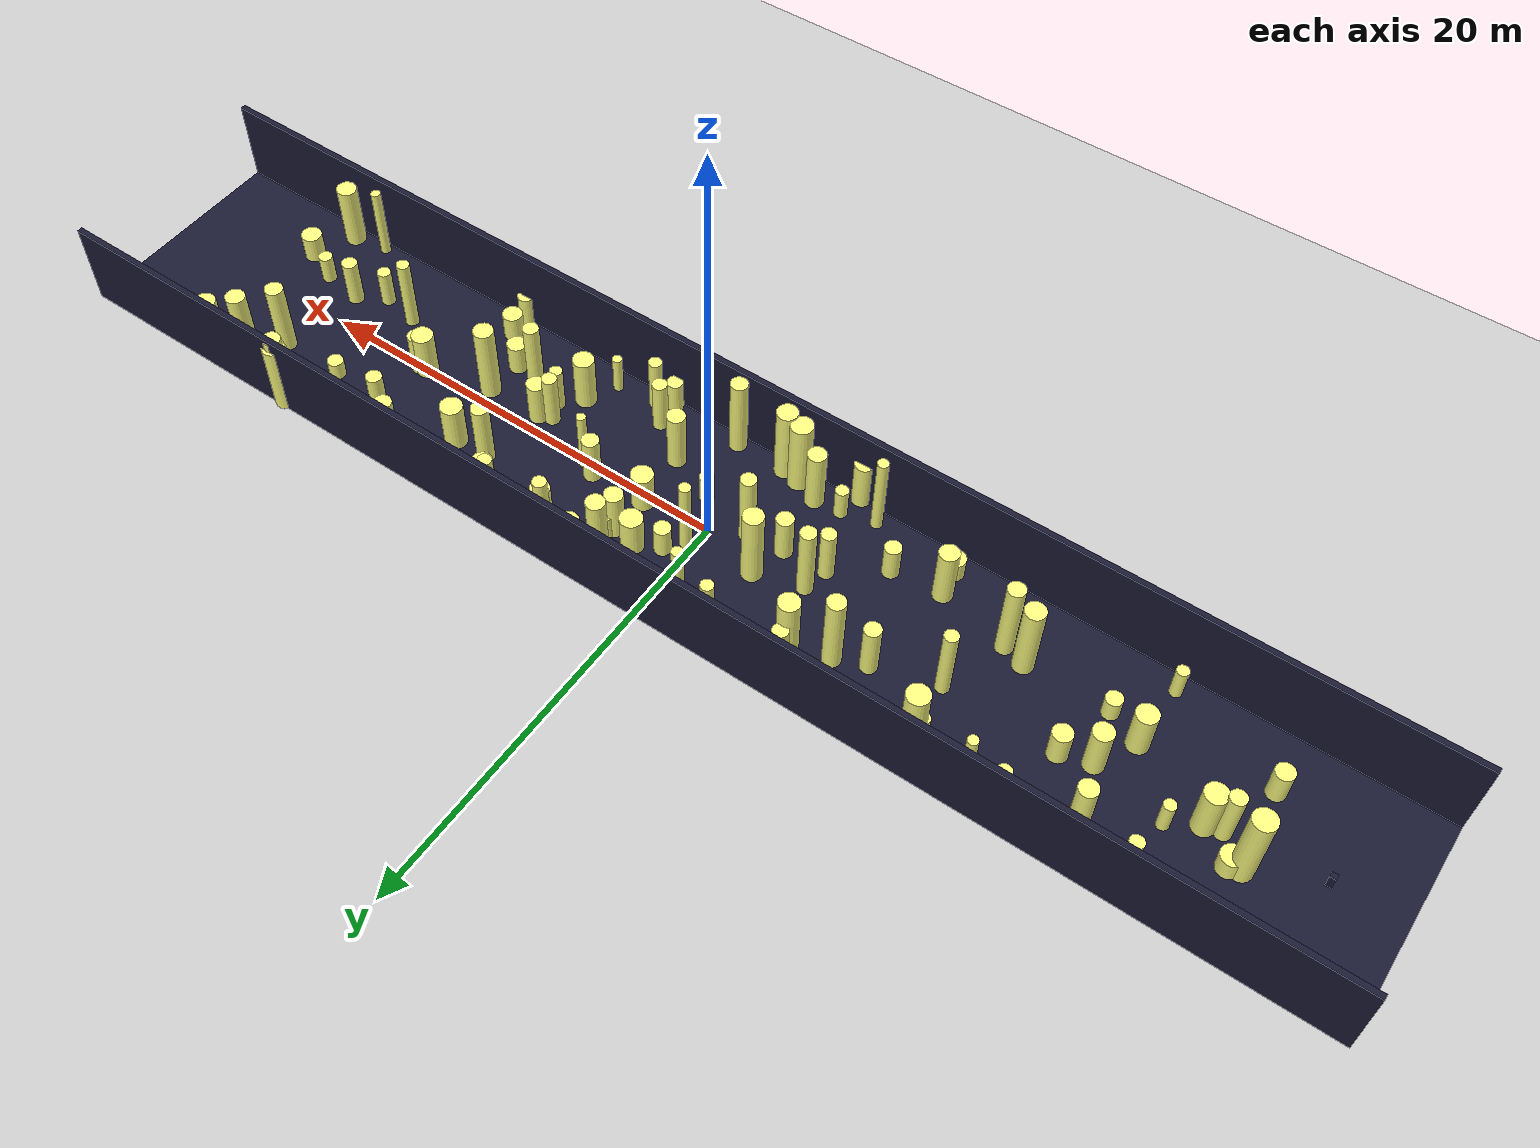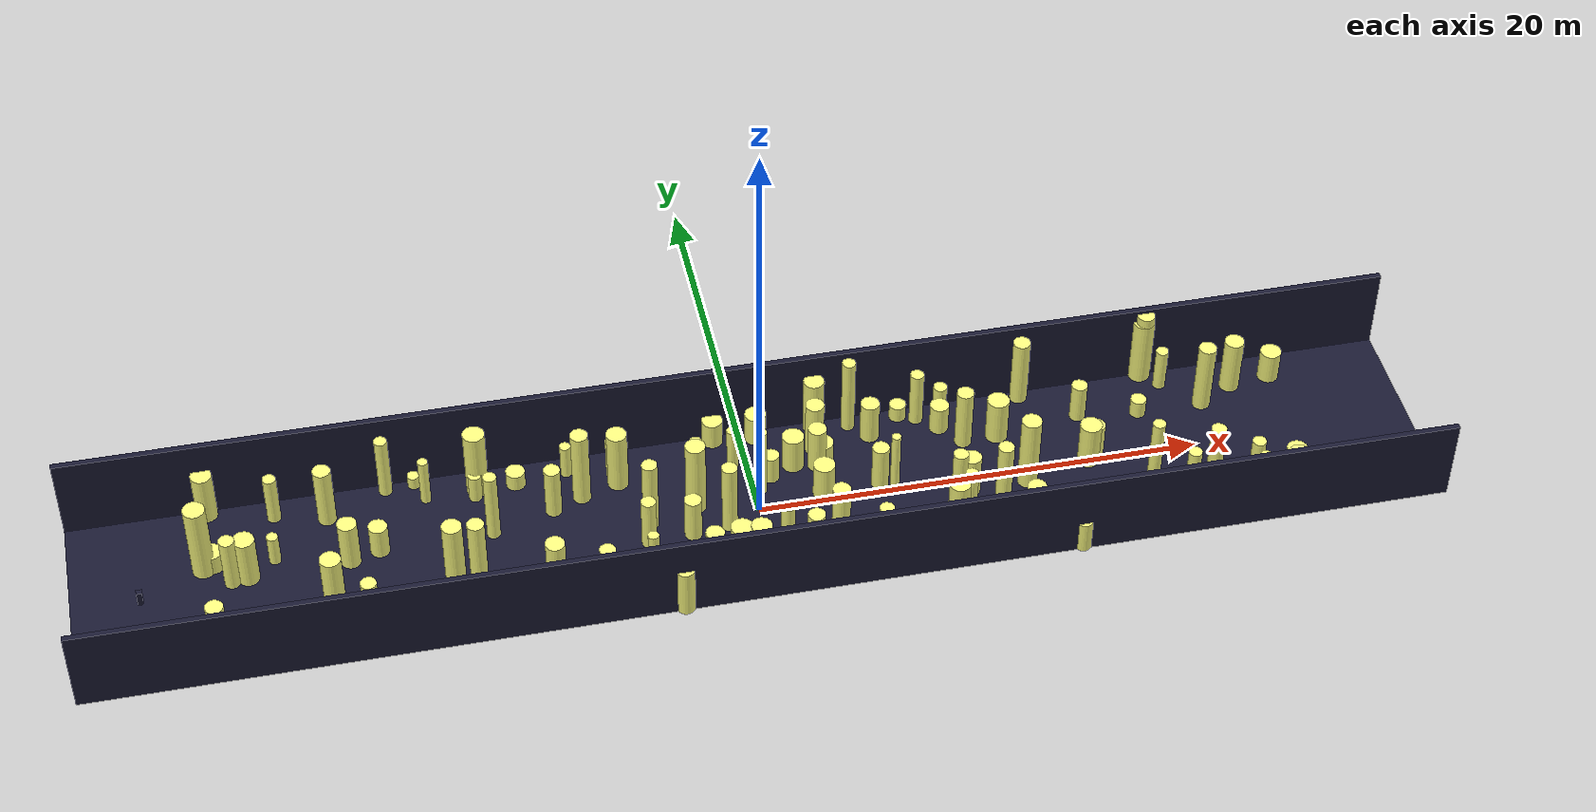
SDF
<?xml version="1.0"?>
<sdf version="1.4">
  <world name="default">
    <gui>
      <camera name="user_camera">
        <pose>-20 -30 40 0 0.66 0.83</pose>
      </camera>
    </gui>
    <include>
      <uri>model://ground_plane</uri>
    </include>
    <include>
      <uri>model://sun</uri>
    </include>
    <scene>
      <shadows>0</shadows>
    </scene>
    <model name="forest">
      <static>true</static>
      <link name="cylinder0">
        <pose>-7.147886534539268 -2.53039150123728 0.845977990508326 0 0 0 </pose>
        <visual name="visual">
          <geometry>
            <cylinder>
              <radius>0.36100098902438316</radius>
              <length>1.691955981016652</length>
            </cylinder>
          </geometry>
          <material>
            <ambient>0.6 0.6 0.6 1</ambient>
            <diffuse>1 1 0.5 1</diffuse>
            <specular>0 0 0</specular>
            <emissive>0 0 0 1</emissive>
          </material>
        </visual>
        <collision name="collision">
          <geometry>
            <cylinder>
              <radius>0.36100098902438316</radius>
              <length>1.691955981016652</length>
            </cylinder>
          </geometry>
          <max_contacts>0</max_contacts>
        </collision>
      </link>
      <link name="cylinder1">
        <pose>8.066118839846212 4.0618754545201 1.4364087561074292 0 0 0 </pose>
        <visual name="visual">
          <geometry>
            <cylinder>
              <radius>0.30672156006113743</radius>
              <length>2.8728175122148585</length>
            </cylinder>
          </geometry>
          <material>
            <ambient>0.6 0.6 0.6 1</ambient>
            <diffuse>1 1 0.5 1</diffuse>
            <specular>0 0 0</specular>
            <emissive>0 0 0 1</emissive>
          </material>
        </visual>
        <collision name="collision">
          <geometry>
            <cylinder>
              <radius>0.30672156006113743</radius>
              <length>2.8728175122148585</length>
            </cylinder>
          </geometry>
          <max_contacts>0</max_contacts>
        </collision>
      </link>
      <link name="cylinder2">
        <pose>-24.197159666264607 1.3272143405766803 1.9146052500122712 0 0 0 </pose>
        <visual name="visual">
          <geometry>
            <cylinder>
              <radius>0.4884541443533371</radius>
              <length>3.8292105000245424</length>
            </cylinder>
          </geometry>
          <material>
            <ambient>0.6 0.6 0.6 1</ambient>
            <diffuse>1 1 0.5 1</diffuse>
            <specular>0 0 0</specular>
            <emissive>0 0 0 1</emissive>
          </material>
        </visual>
        <collision name="collision">
          <geometry>
            <cylinder>
              <radius>0.4884541443533371</radius>
              <length>3.8292105000245424</length>
            </cylinder>
          </geometry>
          <max_contacts>0</max_contacts>
        </collision>
      </link>
      <link name="cylinder3">
        <pose>3.170140923489946 -2.216576093013055 1.4581455485064332 0 0 0 </pose>
        <visual name="visual">
          <geometry>
            <cylinder>
              <radius>0.4053678825190724</radius>
              <length>2.9162910970128664</length>
            </cylinder>
          </geometry>
          <material>
            <ambient>0.6 0.6 0.6 1</ambient>
            <diffuse>1 1 0.5 1</diffuse>
            <specular>0 0 0</specular>
            <emissive>0 0 0 1</emissive>
          </material>
        </visual>
        <collision name="collision">
          <geometry>
            <cylinder>
              <radius>0.4053678825190724</radius>
              <length>2.9162910970128664</length>
            </cylinder>
          </geometry>
          <max_contacts>0</max_contacts>
        </collision>
      </link>
      <link name="cylinder4">
        <pose>9.811674742614109 2.254812388897731 1.5549798884222428 0 0 0 </pose>
        <visual name="visual">
          <geometry>
            <cylinder>
              <radius>0.38145817483813893</radius>
              <length>3.1099597768444855</length>
            </cylinder>
          </geometry>
          <material>
            <ambient>0.6 0.6 0.6 1</ambient>
            <diffuse>1 1 0.5 1</diffuse>
            <specular>0 0 0</specular>
            <emissive>0 0 0 1</emissive>
          </material>
        </visual>
        <collision name="collision">
          <geometry>
            <cylinder>
              <radius>0.38145817483813893</radius>
              <length>3.1099597768444855</length>
            </cylinder>
          </geometry>
          <max_contacts>0</max_contacts>
        </collision>
      </link>
      <link name="cylinder5">
        <pose>-11.634523558374493 0.9237280479130439 1.7960632908729977 0 0 0 </pose>
        <visual name="visual">
          <geometry>
            <cylinder>
              <radius>0.29968947669378615</radius>
              <length>3.5921265817459953</length>
            </cylinder>
          </geometry>
          <material>
            <ambient>0.6 0.6 0.6 1</ambient>
            <diffuse>1 1 0.5 1</diffuse>
            <specular>0 0 0</specular>
            <emissive>0 0 0 1</emissive>
          </material>
        </visual>
        <collision name="collision">
          <geometry>
            <cylinder>
              <radius>0.29968947669378615</radius>
              <length>3.5921265817459953</length>
            </cylinder>
          </geometry>
          <max_contacts>0</max_contacts>
        </collision>
      </link>
      <link name="cylinder6">
        <pose>11.828730259959649 -3.240151185704457 0.5319828385935281 0 0 0 </pose>
        <visual name="visual">
          <geometry>
            <cylinder>
              <radius>0.2554180020215281</radius>
              <length>1.0639656771870563</length>
            </cylinder>
          </geometry>
          <material>
            <ambient>0.6 0.6 0.6 1</ambient>
            <diffuse>1 1 0.5 1</diffuse>
            <specular>0 0 0</specular>
            <emissive>0 0 0 1</emissive>
          </material>
        </visual>
        <collision name="collision">
          <geometry>
            <cylinder>
              <radius>0.2554180020215281</radius>
              <length>1.0639656771870563</length>
            </cylinder>
          </geometry>
          <max_contacts>0</max_contacts>
        </collision>
      </link>
      <link name="cylinder7">
        <pose>-7.947823731998888 3.9267993449656036 0.8813694830557257 0 0 0 </pose>
        <visual name="visual">
          <geometry>
            <cylinder>
              <radius>0.2509167633498099</radius>
              <length>1.7627389661114514</length>
            </cylinder>
          </geometry>
          <material>
            <ambient>0.6 0.6 0.6 1</ambient>
            <diffuse>1 1 0.5 1</diffuse>
            <specular>0 0 0</specular>
            <emissive>0 0 0 1</emissive>
          </material>
        </visual>
        <collision name="collision">
          <geometry>
            <cylinder>
              <radius>0.2509167633498099</radius>
              <length>1.7627389661114514</length>
            </cylinder>
          </geometry>
          <max_contacts>0</max_contacts>
        </collision>
      </link>
      <link name="cylinder8">
        <pose>-14.677818050004776 4.583228677735381 0.33715706794976424 0 0 0 </pose>
        <visual name="visual">
          <geometry>
            <cylinder>
              <radius>0.2694139086498926</radius>
              <length>0.6743141358995285</length>
            </cylinder>
          </geometry>
          <material>
            <ambient>0.6 0.6 0.6 1</ambient>
            <diffuse>1 1 0.5 1</diffuse>
            <specular>0 0 0</specular>
            <emissive>0 0 0 1</emissive>
          </material>
        </visual>
        <collision name="collision">
          <geometry>
            <cylinder>
              <radius>0.2694139086498926</radius>
              <length>0.6743141358995285</length>
            </cylinder>
          </geometry>
          <max_contacts>0</max_contacts>
        </collision>
      </link>
      <link name="cylinder9">
        <pose>-17.915631698224093 0.5598385905810517 1.2128856563475805 0 0 0 </pose>
        <visual name="visual">
          <geometry>
            <cylinder>
              <radius>0.43290104651045036</radius>
              <length>2.425771312695161</length>
            </cylinder>
          </geometry>
          <material>
            <ambient>0.6 0.6 0.6 1</ambient>
            <diffuse>1 1 0.5 1</diffuse>
            <specular>0 0 0</specular>
            <emissive>0 0 0 1</emissive>
          </material>
        </visual>
        <collision name="collision">
          <geometry>
            <cylinder>
              <radius>0.43290104651045036</radius>
              <length>2.425771312695161</length>
            </cylinder>
          </geometry>
          <max_contacts>0</max_contacts>
        </collision>
      </link>
      <link name="cylinder10">
        <pose>-5.416344252856518 -4.228232625096861 1.9914165028328275 0 0 0 </pose>
        <visual name="visual">
          <geometry>
            <cylinder>
              <radius>0.2437314491117159</radius>
              <length>3.982833005665655</length>
            </cylinder>
          </geometry>
          <material>
            <ambient>0.6 0.6 0.6 1</ambient>
            <diffuse>1 1 0.5 1</diffuse>
            <specular>0 0 0</specular>
            <emissive>0 0 0 1</emissive>
          </material>
        </visual>
        <collision name="collision">
          <geometry>
            <cylinder>
              <radius>0.2437314491117159</radius>
              <length>3.982833005665655</length>
            </cylinder>
          </geometry>
          <max_contacts>0</max_contacts>
        </collision>
      </link>
      <link name="cylinder11">
        <pose>15.0008586744622 -0.014582381675227296 1.1326069262630196 0 0 0 </pose>
        <visual name="visual">
          <geometry>
            <cylinder>
              <radius>0.4873311858263697</radius>
              <length>2.2652138525260392</length>
            </cylinder>
          </geometry>
          <material>
            <ambient>0.6 0.6 0.6 1</ambient>
            <diffuse>1 1 0.5 1</diffuse>
            <specular>0 0 0</specular>
            <emissive>0 0 0 1</emissive>
          </material>
        </visual>
        <collision name="collision">
          <geometry>
            <cylinder>
              <radius>0.4873311858263697</radius>
              <length>2.2652138525260392</length>
            </cylinder>
          </geometry>
          <max_contacts>0</max_contacts>
        </collision>
      </link>
      <link name="cylinder12">
        <pose>5.735921058464587 -4.238797580088827 1.3454991109490377 0 0 0 </pose>
        <visual name="visual">
          <geometry>
            <cylinder>
              <radius>0.29776435941849366</radius>
              <length>2.6909982218980755</length>
            </cylinder>
          </geometry>
          <material>
            <ambient>0.6 0.6 0.6 1</ambient>
            <diffuse>1 1 0.5 1</diffuse>
            <specular>0 0 0</specular>
            <emissive>0 0 0 1</emissive>
          </material>
        </visual>
        <collision name="collision">
          <geometry>
            <cylinder>
              <radius>0.29776435941849366</radius>
              <length>2.6909982218980755</length>
            </cylinder>
          </geometry>
          <max_contacts>0</max_contacts>
        </collision>
      </link>
      <link name="cylinder13">
        <pose>-11.945485515646459 3.7343543377362014 1.7563379325139488 0 0 0 </pose>
        <visual name="visual">
          <geometry>
            <cylinder>
              <radius>0.48947886703015514</radius>
              <length>3.5126758650278975</length>
            </cylinder>
          </geometry>
          <material>
            <ambient>0.6 0.6 0.6 1</ambient>
            <diffuse>1 1 0.5 1</diffuse>
            <specular>0 0 0</specular>
            <emissive>0 0 0 1</emissive>
          </material>
        </visual>
        <collision name="collision">
          <geometry>
            <cylinder>
              <radius>0.48947886703015514</radius>
              <length>3.5126758650278975</length>
            </cylinder>
          </geometry>
          <max_contacts>0</max_contacts>
        </collision>
      </link>
      <link name="cylinder14">
        <pose>13.283649940602913 -3.8660855455151024 0.6704017006859668 0 0 0 </pose>
        <visual name="visual">
          <geometry>
            <cylinder>
              <radius>0.4441620345468562</radius>
              <length>1.3408034013719337</length>
            </cylinder>
          </geometry>
          <material>
            <ambient>0.6 0.6 0.6 1</ambient>
            <diffuse>1 1 0.5 1</diffuse>
            <specular>0 0 0</specular>
            <emissive>0 0 0 1</emissive>
          </material>
        </visual>
        <collision name="collision">
          <geometry>
            <cylinder>
              <radius>0.4441620345468562</radius>
              <length>1.3408034013719337</length>
            </cylinder>
          </geometry>
          <max_contacts>0</max_contacts>
        </collision>
      </link>
      <link name="cylinder15">
        <pose>12.987337972857787 4.493687276730903 1.7412392908020857 0 0 0 </pose>
        <visual name="visual">
          <geometry>
            <cylinder>
              <radius>0.38889533113581276</radius>
              <length>3.4824785816041715</length>
            </cylinder>
          </geometry>
          <material>
            <ambient>0.6 0.6 0.6 1</ambient>
            <diffuse>1 1 0.5 1</diffuse>
            <specular>0 0 0</specular>
            <emissive>0 0 0 1</emissive>
          </material>
        </visual>
        <collision name="collision">
          <geometry>
            <cylinder>
              <radius>0.38889533113581276</radius>
              <length>3.4824785816041715</length>
            </cylinder>
          </geometry>
          <max_contacts>0</max_contacts>
        </collision>
      </link>
      <link name="cylinder16">
        <pose>17.465234175828172 -1.820906253466669 1.7901525439202262 0 0 0 </pose>
        <visual name="visual">
          <geometry>
            <cylinder>
              <radius>0.28865827153307433</radius>
              <length>3.5803050878404523</length>
            </cylinder>
          </geometry>
          <material>
            <ambient>0.6 0.6 0.6 1</ambient>
            <diffuse>1 1 0.5 1</diffuse>
            <specular>0 0 0</specular>
            <emissive>0 0 0 1</emissive>
          </material>
        </visual>
        <collision name="collision">
          <geometry>
            <cylinder>
              <radius>0.28865827153307433</radius>
              <length>3.5803050878404523</length>
            </cylinder>
          </geometry>
          <max_contacts>0</max_contacts>
        </collision>
      </link>
      <link name="cylinder17">
        <pose>-0.6109958181470958 2.893471025168205 1.1248857542525301 0 0 0 </pose>
        <visual name="visual">
          <geometry>
            <cylinder>
              <radius>0.26172611279897906</radius>
              <length>2.2497715085050602</length>
            </cylinder>
          </geometry>
          <material>
            <ambient>0.6 0.6 0.6 1</ambient>
            <diffuse>1 1 0.5 1</diffuse>
            <specular>0 0 0</specular>
            <emissive>0 0 0 1</emissive>
          </material>
        </visual>
        <collision name="collision">
          <geometry>
            <cylinder>
              <radius>0.26172611279897906</radius>
              <length>2.2497715085050602</length>
            </cylinder>
          </geometry>
          <max_contacts>0</max_contacts>
        </collision>
      </link>
      <link name="cylinder18">
        <pose>18.850633381991997 4.760175011194956 1.896688940215597 0 0 0 </pose>
        <visual name="visual">
          <geometry>
            <cylinder>
              <radius>0.39927710213772893</radius>
              <length>3.793377880431194</length>
            </cylinder>
          </geometry>
          <material>
            <ambient>0.6 0.6 0.6 1</ambient>
            <diffuse>1 1 0.5 1</diffuse>
            <specular>0 0 0</specular>
            <emissive>0 0 0 1</emissive>
          </material>
        </visual>
        <collision name="collision">
          <geometry>
            <cylinder>
              <radius>0.39927710213772893</radius>
              <length>3.793377880431194</length>
            </cylinder>
          </geometry>
          <max_contacts>0</max_contacts>
        </collision>
      </link>
      <link name="cylinder19">
        <pose>-4.811086742201603 0.12453934173678682 1.8541494410820585 0 0 0 </pose>
        <visual name="visual">
          <geometry>
            <cylinder>
              <radius>0.34894162981649934</radius>
              <length>3.708298882164117</length>
            </cylinder>
          </geometry>
          <material>
            <ambient>0.6 0.6 0.6 1</ambient>
            <diffuse>1 1 0.5 1</diffuse>
            <specular>0 0 0</specular>
            <emissive>0 0 0 1</emissive>
          </material>
        </visual>
        <collision name="collision">
          <geometry>
            <cylinder>
              <radius>0.34894162981649934</radius>
              <length>3.708298882164117</length>
            </cylinder>
          </geometry>
          <max_contacts>0</max_contacts>
        </collision>
      </link>
      <link name="cylinder20">
        <pose>-10.241238511680573 3.7366486437823987 0.4324220582112719 0 0 0 </pose>
        <visual name="visual">
          <geometry>
            <cylinder>
              <radius>0.43045122246468775</radius>
              <length>0.8648441164225438</length>
            </cylinder>
          </geometry>
          <material>
            <ambient>0.6 0.6 0.6 1</ambient>
            <diffuse>1 1 0.5 1</diffuse>
            <specular>0 0 0</specular>
            <emissive>0 0 0 1</emissive>
          </material>
        </visual>
        <collision name="collision">
          <geometry>
            <cylinder>
              <radius>0.43045122246468775</radius>
              <length>0.8648441164225438</length>
            </cylinder>
          </geometry>
          <max_contacts>0</max_contacts>
        </collision>
      </link>
      <link name="cylinder21">
        <pose>18.02866879839089 2.437116368702269 0.46491452243994297 0 0 0 </pose>
        <visual name="visual">
          <geometry>
            <cylinder>
              <radius>0.3569830298765556</radius>
              <length>0.9298290448798859</length>
            </cylinder>
          </geometry>
          <material>
            <ambient>0.6 0.6 0.6 1</ambient>
            <diffuse>1 1 0.5 1</diffuse>
            <specular>0 0 0</specular>
            <emissive>0 0 0 1</emissive>
          </material>
        </visual>
        <collision name="collision">
          <geometry>
            <cylinder>
              <radius>0.3569830298765556</radius>
              <length>0.9298290448798859</length>
            </cylinder>
          </geometry>
          <max_contacts>0</max_contacts>
        </collision>
      </link>
      <link name="cylinder22">
        <pose>15.317636051968876 0.08138888489696594 1.0537577487184902 0 0 0 </pose>
        <visual name="visual">
          <geometry>
            <cylinder>
              <radius>0.3703493254064486</radius>
              <length>2.1075154974369803</length>
            </cylinder>
          </geometry>
          <material>
            <ambient>0.6 0.6 0.6 1</ambient>
            <diffuse>1 1 0.5 1</diffuse>
            <specular>0 0 0</specular>
            <emissive>0 0 0 1</emissive>
          </material>
        </visual>
        <collision name="collision">
          <geometry>
            <cylinder>
              <radius>0.3703493254064486</radius>
              <length>2.1075154974369803</length>
            </cylinder>
          </geometry>
          <max_contacts>0</max_contacts>
        </collision>
      </link>
      <link name="cylinder23">
        <pose>-1.6142446024644812 -4.231911779642243 1.8334374162560612 0 0 0 </pose>
        <visual name="visual">
          <geometry>
            <cylinder>
              <radius>0.49649550393206016</radius>
              <length>3.6668748325121223</length>
            </cylinder>
          </geometry>
          <material>
            <ambient>0.6 0.6 0.6 1</ambient>
            <diffuse>1 1 0.5 1</diffuse>
            <specular>0 0 0</specular>
            <emissive>0 0 0 1</emissive>
          </material>
        </visual>
        <collision name="collision">
          <geometry>
            <cylinder>
              <radius>0.49649550393206016</radius>
              <length>3.6668748325121223</length>
            </cylinder>
          </geometry>
          <max_contacts>0</max_contacts>
        </collision>
      </link>
      <link name="cylinder24">
        <pose>-16.60672865435462 0.9425299335206745 0.7955071776099385 0 0 0 </pose>
        <visual name="visual">
          <geometry>
            <cylinder>
              <radius>0.42145514431712705</radius>
              <length>1.591014355219877</length>
            </cylinder>
          </geometry>
          <material>
            <ambient>0.6 0.6 0.6 1</ambient>
            <diffuse>1 1 0.5 1</diffuse>
            <specular>0 0 0</specular>
            <emissive>0 0 0 1</emissive>
          </material>
        </visual>
        <collision name="collision">
          <geometry>
            <cylinder>
              <radius>0.42145514431712705</radius>
              <length>1.591014355219877</length>
            </cylinder>
          </geometry>
          <max_contacts>0</max_contacts>
        </collision>
      </link>
      <link name="cylinder25">
        <pose>11.895203911824616 -2.475094329204822 0.7576453206853451 0 0 0 </pose>
        <visual name="visual">
          <geometry>
            <cylinder>
              <radius>0.4295975941818696</radius>
              <length>1.5152906413706901</length>
            </cylinder>
          </geometry>
          <material>
            <ambient>0.6 0.6 0.6 1</ambient>
            <diffuse>1 1 0.5 1</diffuse>
            <specular>0 0 0</specular>
            <emissive>0 0 0 1</emissive>
          </material>
        </visual>
        <collision name="collision">
          <geometry>
            <cylinder>
              <radius>0.4295975941818696</radius>
              <length>1.5152906413706901</length>
            </cylinder>
          </geometry>
          <max_contacts>0</max_contacts>
        </collision>
      </link>
      <link name="cylinder26">
        <pose>-23.797057718114523 4.625745168727798 1.2628731413633818 0 0 0 </pose>
        <visual name="visual">
          <geometry>
            <cylinder>
              <radius>0.4680871777554617</radius>
              <length>2.5257462827267636</length>
            </cylinder>
          </geometry>
          <material>
            <ambient>0.6 0.6 0.6 1</ambient>
            <diffuse>1 1 0.5 1</diffuse>
            <specular>0 0 0</specular>
            <emissive>0 0 0 1</emissive>
          </material>
        </visual>
        <collision name="collision">
          <geometry>
            <cylinder>
              <radius>0.4680871777554617</radius>
              <length>2.5257462827267636</length>
            </cylinder>
          </geometry>
          <max_contacts>0</max_contacts>
        </collision>
      </link>
      <link name="cylinder27">
        <pose>22.644880289418985 3.302533713791421 1.4079278390467205 0 0 0 </pose>
        <visual name="visual">
          <geometry>
            <cylinder>
              <radius>0.4429732584940284</radius>
              <length>2.815855678093441</length>
            </cylinder>
          </geometry>
          <material>
            <ambient>0.6 0.6 0.6 1</ambient>
            <diffuse>1 1 0.5 1</diffuse>
            <specular>0 0 0</specular>
            <emissive>0 0 0 1</emissive>
          </material>
        </visual>
        <collision name="collision">
          <geometry>
            <cylinder>
              <radius>0.4429732584940284</radius>
              <length>2.815855678093441</length>
            </cylinder>
          </geometry>
          <max_contacts>0</max_contacts>
        </collision>
      </link>
      <link name="cylinder28">
        <pose>23.089459009583173 -4.303348235721679 1.5611952416324024 0 0 0 </pose>
        <visual name="visual">
          <geometry>
            <cylinder>
              <radius>0.45974052555895284</radius>
              <length>3.122390483264805</length>
            </cylinder>
          </geometry>
          <material>
            <ambient>0.6 0.6 0.6 1</ambient>
            <diffuse>1 1 0.5 1</diffuse>
            <specular>0 0 0</specular>
            <emissive>0 0 0 1</emissive>
          </material>
        </visual>
        <collision name="collision">
          <geometry>
            <cylinder>
              <radius>0.45974052555895284</radius>
              <length>3.122390483264805</length>
            </cylinder>
          </geometry>
          <max_contacts>0</max_contacts>
        </collision>
      </link>
      <link name="cylinder29">
        <pose>2.9944841728109957 0.37837275598541176 0.9362592487458747 0 0 0 </pose>
        <visual name="visual">
          <geometry>
            <cylinder>
              <radius>0.48791380645112986</radius>
              <length>1.8725184974917495</length>
            </cylinder>
          </geometry>
          <material>
            <ambient>0.6 0.6 0.6 1</ambient>
            <diffuse>1 1 0.5 1</diffuse>
            <specular>0 0 0</specular>
            <emissive>0 0 0 1</emissive>
          </material>
        </visual>
        <collision name="collision">
          <geometry>
            <cylinder>
              <radius>0.48791380645112986</radius>
              <length>1.8725184974917495</length>
            </cylinder>
          </geometry>
          <max_contacts>0</max_contacts>
        </collision>
      </link>
      <link name="cylinder30">
        <pose>8.803131889629185 -0.9608375173800159 1.3262918288286945 0 0 0 </pose>
        <visual name="visual">
          <geometry>
            <cylinder>
              <radius>0.3345717851911674</radius>
              <length>2.652583657657389</length>
            </cylinder>
          </geometry>
          <material>
            <ambient>0.6 0.6 0.6 1</ambient>
            <diffuse>1 1 0.5 1</diffuse>
            <specular>0 0 0</specular>
            <emissive>0 0 0 1</emissive>
          </material>
        </visual>
        <collision name="collision">
          <geometry>
            <cylinder>
              <radius>0.3345717851911674</radius>
              <length>2.652583657657389</length>
            </cylinder>
          </geometry>
          <max_contacts>0</max_contacts>
        </collision>
      </link>
      <link name="cylinder31">
        <pose>-23.780388621568203 1.4876228525524295 0.4973699896182534 0 0 0 </pose>
        <visual name="visual">
          <geometry>
            <cylinder>
              <radius>0.4775433015344443</radius>
              <length>0.9947399792365068</length>
            </cylinder>
          </geometry>
          <material>
            <ambient>0.6 0.6 0.6 1</ambient>
            <diffuse>1 1 0.5 1</diffuse>
            <specular>0 0 0</specular>
            <emissive>0 0 0 1</emissive>
          </material>
        </visual>
        <collision name="collision">
          <geometry>
            <cylinder>
              <radius>0.4775433015344443</radius>
              <length>0.9947399792365068</length>
            </cylinder>
          </geometry>
          <max_contacts>0</max_contacts>
        </collision>
      </link>
      <link name="cylinder32">
        <pose>-1.455620772731276 -0.7115622017840115 1.835701524792615 0 0 0 </pose>
        <visual name="visual">
          <geometry>
            <cylinder>
              <radius>0.3483356824140912</radius>
              <length>3.67140304958523</length>
            </cylinder>
          </geometry>
          <material>
            <ambient>0.6 0.6 0.6 1</ambient>
            <diffuse>1 1 0.5 1</diffuse>
            <specular>0 0 0</specular>
            <emissive>0 0 0 1</emissive>
          </material>
        </visual>
        <collision name="collision">
          <geometry>
            <cylinder>
              <radius>0.3483356824140912</radius>
              <length>3.67140304958523</length>
            </cylinder>
          </geometry>
          <max_contacts>0</max_contacts>
        </collision>
      </link>
      <link name="cylinder33">
        <pose>5.778091470431633 3.467242111142605 1.0503981685899615 0 0 0 </pose>
        <visual name="visual">
          <geometry>
            <cylinder>
              <radius>0.4259204351675813</radius>
              <length>2.100796337179923</length>
            </cylinder>
          </geometry>
          <material>
            <ambient>0.6 0.6 0.6 1</ambient>
            <diffuse>1 1 0.5 1</diffuse>
            <specular>0 0 0</specular>
            <emissive>0 0 0 1</emissive>
          </material>
        </visual>
        <collision name="collision">
          <geometry>
            <cylinder>
              <radius>0.4259204351675813</radius>
              <length>2.100796337179923</length>
            </cylinder>
          </geometry>
          <max_contacts>0</max_contacts>
        </collision>
      </link>
      <link name="cylinder34">
        <pose>8.325086826868251 -2.668230914443628 1.3018618476149957 0 0 0 </pose>
        <visual name="visual">
          <geometry>
            <cylinder>
              <radius>0.4680022684746793</radius>
              <length>2.6037236952299914</length>
            </cylinder>
          </geometry>
          <material>
            <ambient>0.6 0.6 0.6 1</ambient>
            <diffuse>1 1 0.5 1</diffuse>
            <specular>0 0 0</specular>
            <emissive>0 0 0 1</emissive>
          </material>
        </visual>
        <collision name="collision">
          <geometry>
            <cylinder>
              <radius>0.4680022684746793</radius>
              <length>2.6037236952299914</length>
            </cylinder>
          </geometry>
          <max_contacts>0</max_contacts>
        </collision>
      </link>
      <link name="cylinder35">
        <pose>1.5702695720020579 -4.402047520439972 1.9614032190515487 0 0 0 </pose>
        <visual name="visual">
          <geometry>
            <cylinder>
              <radius>0.3827382010326946</radius>
              <length>3.9228064381030974</length>
            </cylinder>
          </geometry>
          <material>
            <ambient>0.6 0.6 0.6 1</ambient>
            <diffuse>1 1 0.5 1</diffuse>
            <specular>0 0 0</specular>
            <emissive>0 0 0 1</emissive>
          </material>
        </visual>
        <collision name="collision">
          <geometry>
            <cylinder>
              <radius>0.3827382010326946</radius>
              <length>3.9228064381030974</length>
            </cylinder>
          </geometry>
          <max_contacts>0</max_contacts>
        </collision>
      </link>
      <link name="cylinder36">
        <pose>23.86629952842967 -2.405696458742531 0.6725989420630607 0 0 0 </pose>
        <visual name="visual">
          <geometry>
            <cylinder>
              <radius>0.4671781323828896</radius>
              <length>1.3451978841261214</length>
            </cylinder>
          </geometry>
          <material>
            <ambient>0.6 0.6 0.6 1</ambient>
            <diffuse>1 1 0.5 1</diffuse>
            <specular>0 0 0</specular>
            <emissive>0 0 0 1</emissive>
          </material>
        </visual>
        <collision name="collision">
          <geometry>
            <cylinder>
              <radius>0.4671781323828896</radius>
              <length>1.3451978841261214</length>
            </cylinder>
          </geometry>
          <max_contacts>0</max_contacts>
        </collision>
      </link>
      <link name="cylinder37">
        <pose>-2.227156157283801 3.162929607211302 0.8202759994643201 0 0 0 </pose>
        <visual name="visual">
          <geometry>
            <cylinder>
              <radius>0.2883059270450284</radius>
              <length>1.6405519989286401</length>
            </cylinder>
          </geometry>
          <material>
            <ambient>0.6 0.6 0.6 1</ambient>
            <diffuse>1 1 0.5 1</diffuse>
            <specular>0 0 0</specular>
            <emissive>0 0 0 1</emissive>
          </material>
        </visual>
        <collision name="collision">
          <geometry>
            <cylinder>
              <radius>0.2883059270450284</radius>
              <length>1.6405519989286401</length>
            </cylinder>
          </geometry>
          <max_contacts>0</max_contacts>
        </collision>
      </link>
      <link name="cylinder38">
        <pose>-12.093552864069684 3.2888989436351252 0.713672998915895 0 0 0 </pose>
        <visual name="visual">
          <geometry>
            <cylinder>
              <radius>0.29613382893907125</radius>
              <length>1.42734599783179</length>
            </cylinder>
          </geometry>
          <material>
            <ambient>0.6 0.6 0.6 1</ambient>
            <diffuse>1 1 0.5 1</diffuse>
            <specular>0 0 0</specular>
            <emissive>0 0 0 1</emissive>
          </material>
        </visual>
        <collision name="collision">
          <geometry>
            <cylinder>
              <radius>0.29613382893907125</radius>
              <length>1.42734599783179</length>
            </cylinder>
          </geometry>
          <max_contacts>0</max_contacts>
        </collision>
      </link>
      <link name="cylinder39">
        <pose>13.354917076665004 -4.925235537709143 0.7724096318504798 0 0 0 </pose>
        <visual name="visual">
          <geometry>
            <cylinder>
              <radius>0.37187433411628046</radius>
              <length>1.5448192637009597</length>
            </cylinder>
          </geometry>
          <material>
            <ambient>0.6 0.6 0.6 1</ambient>
            <diffuse>1 1 0.5 1</diffuse>
            <specular>0 0 0</specular>
            <emissive>0 0 0 1</emissive>
          </material>
        </visual>
        <collision name="collision">
          <geometry>
            <cylinder>
              <radius>0.37187433411628046</radius>
              <length>1.5448192637009597</length>
            </cylinder>
          </geometry>
          <max_contacts>0</max_contacts>
        </collision>
      </link>
      <link name="cylinder40">
        <pose>3.4354026957642674 4.5520370584746175 1.4604777693836493 0 0 0 </pose>
        <visual name="visual">
          <geometry>
            <cylinder>
              <radius>0.4684329063424866</radius>
              <length>2.9209555387672985</length>
            </cylinder>
          </geometry>
          <material>
            <ambient>0.6 0.6 0.6 1</ambient>
            <diffuse>1 1 0.5 1</diffuse>
            <specular>0 0 0</specular>
            <emissive>0 0 0 1</emissive>
          </material>
        </visual>
        <collision name="collision">
          <geometry>
            <cylinder>
              <radius>0.4684329063424866</radius>
              <length>2.9209555387672985</length>
            </cylinder>
          </geometry>
          <max_contacts>0</max_contacts>
        </collision>
      </link>
      <link name="cylinder41">
        <pose>1.0098472469576834 -1.3427515907958245 0.7044551769499073 0 0 0 </pose>
        <visual name="visual">
          <geometry>
            <cylinder>
              <radius>0.3154672098886814</radius>
              <length>1.4089103538998147</length>
            </cylinder>
          </geometry>
          <material>
            <ambient>0.6 0.6 0.6 1</ambient>
            <diffuse>1 1 0.5 1</diffuse>
            <specular>0 0 0</specular>
            <emissive>0 0 0 1</emissive>
          </material>
        </visual>
        <collision name="collision">
          <geometry>
            <cylinder>
              <radius>0.3154672098886814</radius>
              <length>1.4089103538998147</length>
            </cylinder>
          </geometry>
          <max_contacts>0</max_contacts>
        </collision>
      </link>
      <link name="cylinder42">
        <pose>6.167972155496681 0.2064080756497333 1.56071031860152 0 0 0 </pose>
        <visual name="visual">
          <geometry>
            <cylinder>
              <radius>0.20504070258508728</radius>
              <length>3.12142063720304</length>
            </cylinder>
          </geometry>
          <material>
            <ambient>0.6 0.6 0.6 1</ambient>
            <diffuse>1 1 0.5 1</diffuse>
            <specular>0 0 0</specular>
            <emissive>0 0 0 1</emissive>
          </material>
        </visual>
        <collision name="collision">
          <geometry>
            <cylinder>
              <radius>0.20504070258508728</radius>
              <length>3.12142063720304</length>
            </cylinder>
          </geometry>
          <max_contacts>0</max_contacts>
        </collision>
      </link>
      <link name="cylinder43">
        <pose>0.7390791805014949 4.401114287455494 0.776004258543322 0 0 0 </pose>
        <visual name="visual">
          <geometry>
            <cylinder>
              <radius>0.487037994986735</radius>
              <length>1.552008517086644</length>
            </cylinder>
          </geometry>
          <material>
            <ambient>0.6 0.6 0.6 1</ambient>
            <diffuse>1 1 0.5 1</diffuse>
            <specular>0 0 0</specular>
            <emissive>0 0 0 1</emissive>
          </material>
        </visual>
        <collision name="collision">
          <geometry>
            <cylinder>
              <radius>0.487037994986735</radius>
              <length>1.552008517086644</length>
            </cylinder>
          </geometry>
          <max_contacts>0</max_contacts>
        </collision>
      </link>
      <link name="cylinder44">
        <pose>-21.121284451458855 1.3014376965214307 0.7716638905629418 0 0 0 </pose>
        <visual name="visual">
          <geometry>
            <cylinder>
              <radius>0.2565426327069845</radius>
              <length>1.5433277811258836</length>
            </cylinder>
          </geometry>
          <material>
            <ambient>0.6 0.6 0.6 1</ambient>
            <diffuse>1 1 0.5 1</diffuse>
            <specular>0 0 0</specular>
            <emissive>0 0 0 1</emissive>
          </material>
        </visual>
        <collision name="collision">
          <geometry>
            <cylinder>
              <radius>0.2565426327069845</radius>
              <length>1.5433277811258836</length>
            </cylinder>
          </geometry>
          <max_contacts>0</max_contacts>
        </collision>
      </link>
      <link name="cylinder45">
        <pose>12.004390138690482 -0.7123755683639166 1.8909977528873547 0 0 0 </pose>
        <visual name="visual">
          <geometry>
            <cylinder>
              <radius>0.4477335801210177</radius>
              <length>3.7819955057747094</length>
            </cylinder>
          </geometry>
          <material>
            <ambient>0.6 0.6 0.6 1</ambient>
            <diffuse>1 1 0.5 1</diffuse>
            <specular>0 0 0</specular>
            <emissive>0 0 0 1</emissive>
          </material>
        </visual>
        <collision name="collision">
          <geometry>
            <cylinder>
              <radius>0.4477335801210177</radius>
              <length>3.7819955057747094</length>
            </cylinder>
          </geometry>
          <max_contacts>0</max_contacts>
        </collision>
      </link>
      <link name="cylinder46">
        <pose>2.026135868582031 2.3939443775527014 0.9225425791103101 0 0 0 </pose>
        <visual name="visual">
          <geometry>
            <cylinder>
              <radius>0.4975333186364069</radius>
              <length>1.8450851582206202</length>
            </cylinder>
          </geometry>
          <material>
            <ambient>0.6 0.6 0.6 1</ambient>
            <diffuse>1 1 0.5 1</diffuse>
            <specular>0 0 0</specular>
            <emissive>0 0 0 1</emissive>
          </material>
        </visual>
        <collision name="collision">
          <geometry>
            <cylinder>
              <radius>0.4975333186364069</radius>
              <length>1.8450851582206202</length>
            </cylinder>
          </geometry>
          <max_contacts>0</max_contacts>
        </collision>
      </link>
      <link name="cylinder47">
        <pose>3.070877339769396 2.156356076204215 1.1729494905168913 0 0 0 </pose>
        <visual name="visual">
          <geometry>
            <cylinder>
              <radius>0.41773534468563417</radius>
              <length>2.3458989810337827</length>
            </cylinder>
          </geometry>
          <material>
            <ambient>0.6 0.6 0.6 1</ambient>
            <diffuse>1 1 0.5 1</diffuse>
            <specular>0 0 0</specular>
            <emissive>0 0 0 1</emissive>
          </material>
        </visual>
        <collision name="collision">
          <geometry>
            <cylinder>
              <radius>0.41773534468563417</radius>
              <length>2.3458989810337827</length>
            </cylinder>
          </geometry>
          <max_contacts>0</max_contacts>
        </collision>
      </link>
      <link name="cylinder48">
        <pose>-9.212835363459954 -3.946797553412603 0.5192304552640402 0 0 0 </pose>
        <visual name="visual">
          <geometry>
            <cylinder>
              <radius>0.45319021435223766</radius>
              <length>1.0384609105280804</length>
            </cylinder>
          </geometry>
          <material>
            <ambient>0.6 0.6 0.6 1</ambient>
            <diffuse>1 1 0.5 1</diffuse>
            <specular>0 0 0</specular>
            <emissive>0 0 0 1</emissive>
          </material>
        </visual>
        <collision name="collision">
          <geometry>
            <cylinder>
              <radius>0.45319021435223766</radius>
              <length>1.0384609105280804</length>
            </cylinder>
          </geometry>
          <max_contacts>0</max_contacts>
        </collision>
      </link>
      <link name="cylinder49">
        <pose>-1.203166292023262 4.591323689585245 0.6818427673470334 0 0 0 </pose>
        <visual name="visual">
          <geometry>
            <cylinder>
              <radius>0.4665640111960839</radius>
              <length>1.3636855346940668</length>
            </cylinder>
          </geometry>
          <material>
            <ambient>0.6 0.6 0.6 1</ambient>
            <diffuse>1 1 0.5 1</diffuse>
            <specular>0 0 0</specular>
            <emissive>0 0 0 1</emissive>
          </material>
        </visual>
        <collision name="collision">
          <geometry>
            <cylinder>
              <radius>0.4665640111960839</radius>
              <length>1.3636855346940668</length>
            </cylinder>
          </geometry>
          <max_contacts>0</max_contacts>
        </collision>
      </link>
      <link name="cylinder50">
        <pose>4.898978094734169 -3.4131946261780977 1.302396155600394 0 0 0 </pose>
        <visual name="visual">
          <geometry>
            <cylinder>
              <radius>0.3321295872910309</radius>
              <length>2.604792311200788</length>
            </cylinder>
          </geometry>
          <material>
            <ambient>0.6 0.6 0.6 1</ambient>
            <diffuse>1 1 0.5 1</diffuse>
            <specular>0 0 0</specular>
            <emissive>0 0 0 1</emissive>
          </material>
        </visual>
        <collision name="collision">
          <geometry>
            <cylinder>
              <radius>0.3321295872910309</radius>
              <length>2.604792311200788</length>
            </cylinder>
          </geometry>
          <max_contacts>0</max_contacts>
        </collision>
      </link>
      <link name="cylinder51">
        <pose>-9.415853639306548 -2.7923139661245977 1.419915691154692 0 0 0 </pose>
        <visual name="visual">
          <geometry>
            <cylinder>
              <radius>0.4297711594989393</radius>
              <length>2.839831382309384</length>
            </cylinder>
          </geometry>
          <material>
            <ambient>0.6 0.6 0.6 1</ambient>
            <diffuse>1 1 0.5 1</diffuse>
            <specular>0 0 0</specular>
            <emissive>0 0 0 1</emissive>
          </material>
        </visual>
        <collision name="collision">
          <geometry>
            <cylinder>
              <radius>0.4297711594989393</radius>
              <length>2.839831382309384</length>
            </cylinder>
          </geometry>
          <max_contacts>0</max_contacts>
        </collision>
      </link>
      <link name="cylinder52">
        <pose>11.380908579508443 2.324919556639858 1.1375491714978354 0 0 0 </pose>
        <visual name="visual">
          <geometry>
            <cylinder>
              <radius>0.49752402711802485</radius>
              <length>2.275098342995671</length>
            </cylinder>
          </geometry>
          <material>
            <ambient>0.6 0.6 0.6 1</ambient>
            <diffuse>1 1 0.5 1</diffuse>
            <specular>0 0 0</specular>
            <emissive>0 0 0 1</emissive>
          </material>
        </visual>
        <collision name="collision">
          <geometry>
            <cylinder>
              <radius>0.49752402711802485</radius>
              <length>2.275098342995671</length>
            </cylinder>
          </geometry>
          <max_contacts>0</max_contacts>
        </collision>
      </link>
      <link name="cylinder53">
        <pose>7.306784133140212 4.43199189034911 0.4163177386689213 0 0 0 </pose>
        <visual name="visual">
          <geometry>
            <cylinder>
              <radius>0.38142704160027086</radius>
              <length>0.8326354773378426</length>
            </cylinder>
          </geometry>
          <material>
            <ambient>0.6 0.6 0.6 1</ambient>
            <diffuse>1 1 0.5 1</diffuse>
            <specular>0 0 0</specular>
            <emissive>0 0 0 1</emissive>
          </material>
        </visual>
        <collision name="collision">
          <geometry>
            <cylinder>
              <radius>0.38142704160027086</radius>
              <length>0.8326354773378426</length>
            </cylinder>
          </geometry>
          <max_contacts>0</max_contacts>
        </collision>
      </link>
      <link name="cylinder54">
        <pose>4.964270226070756 4.297833036703905 1.9822701510709995 0 0 0 </pose>
        <visual name="visual">
          <geometry>
            <cylinder>
              <radius>0.30186791827440784</radius>
              <length>3.964540302141999</length>
            </cylinder>
          </geometry>
          <material>
            <ambient>0.6 0.6 0.6 1</ambient>
            <diffuse>1 1 0.5 1</diffuse>
            <specular>0 0 0</specular>
            <emissive>0 0 0 1</emissive>
          </material>
        </visual>
        <collision name="collision">
          <geometry>
            <cylinder>
              <radius>0.30186791827440784</radius>
              <length>3.964540302141999</length>
            </cylinder>
          </geometry>
          <max_contacts>0</max_contacts>
        </collision>
      </link>
      <link name="cylinder55">
        <pose>-23.89654228058503 -2.2864291057136157 0.7915750081761862 0 0 0 </pose>
        <visual name="visual">
          <geometry>
            <cylinder>
              <radius>0.40266826958794544</radius>
              <length>1.5831500163523724</length>
            </cylinder>
          </geometry>
          <material>
            <ambient>0.6 0.6 0.6 1</ambient>
            <diffuse>1 1 0.5 1</diffuse>
            <specular>0 0 0</specular>
            <emissive>0 0 0 1</emissive>
          </material>
        </visual>
        <collision name="collision">
          <geometry>
            <cylinder>
              <radius>0.40266826958794544</radius>
              <length>1.5831500163523724</length>
            </cylinder>
          </geometry>
          <max_contacts>0</max_contacts>
        </collision>
      </link>
      <link name="cylinder56">
        <pose>-2.6915168860239866 -3.7595114620198276 1.5358558752328402 0 0 0 </pose>
        <visual name="visual">
          <geometry>
            <cylinder>
              <radius>0.4101143226617895</radius>
              <length>3.0717117504656803</length>
            </cylinder>
          </geometry>
          <material>
            <ambient>0.6 0.6 0.6 1</ambient>
            <diffuse>1 1 0.5 1</diffuse>
            <specular>0 0 0</specular>
            <emissive>0 0 0 1</emissive>
          </material>
        </visual>
        <collision name="collision">
          <geometry>
            <cylinder>
              <radius>0.4101143226617895</radius>
              <length>3.0717117504656803</length>
            </cylinder>
          </geometry>
          <max_contacts>0</max_contacts>
        </collision>
      </link>
      <link name="cylinder57">
        <pose>-22.327788307976064 0.49718473346356973 1.230835638447007 0 0 0 </pose>
        <visual name="visual">
          <geometry>
            <cylinder>
              <radius>0.47874811197229566</radius>
              <length>2.461671276894014</length>
            </cylinder>
          </geometry>
          <material>
            <ambient>0.6 0.6 0.6 1</ambient>
            <diffuse>1 1 0.5 1</diffuse>
            <specular>0 0 0</specular>
            <emissive>0 0 0 1</emissive>
          </material>
        </visual>
        <collision name="collision">
          <geometry>
            <cylinder>
              <radius>0.47874811197229566</radius>
              <length>2.461671276894014</length>
            </cylinder>
          </geometry>
          <max_contacts>0</max_contacts>
        </collision>
      </link>
      <link name="cylinder58">
        <pose>-3.1176816136729855 -0.8837401931310964 1.1131635898548498 0 0 0 </pose>
        <visual name="visual">
          <geometry>
            <cylinder>
              <radius>0.38105272283199965</radius>
              <length>2.2263271797096995</length>
            </cylinder>
          </geometry>
          <material>
            <ambient>0.6 0.6 0.6 1</ambient>
            <diffuse>1 1 0.5 1</diffuse>
            <specular>0 0 0</specular>
            <emissive>0 0 0 1</emissive>
          </material>
        </visual>
        <collision name="collision">
          <geometry>
            <cylinder>
              <radius>0.38105272283199965</radius>
              <length>2.2263271797096995</length>
            </cylinder>
          </geometry>
          <max_contacts>0</max_contacts>
        </collision>
      </link>
      <link name="cylinder59">
        <pose>-8.84829752086118 1.7615249106251234 1.3064324709113642 0 0 0 </pose>
        <visual name="visual">
          <geometry>
            <cylinder>
              <radius>0.36413401016565283</radius>
              <length>2.6128649418227283</length>
            </cylinder>
          </geometry>
          <material>
            <ambient>0.6 0.6 0.6 1</ambient>
            <diffuse>1 1 0.5 1</diffuse>
            <specular>0 0 0</specular>
            <emissive>0 0 0 1</emissive>
          </material>
        </visual>
        <collision name="collision">
          <geometry>
            <cylinder>
              <radius>0.36413401016565283</radius>
              <length>2.6128649418227283</length>
            </cylinder>
          </geometry>
          <max_contacts>0</max_contacts>
        </collision>
      </link>
      <link name="cylinder60">
        <pose>-4.218280016733239 -4.955279667334835 1.180016431451273 0 0 0 </pose>
        <visual name="visual">
          <geometry>
            <cylinder>
              <radius>0.4194617668120034</radius>
              <length>2.360032862902546</length>
            </cylinder>
          </geometry>
          <material>
            <ambient>0.6 0.6 0.6 1</ambient>
            <diffuse>1 1 0.5 1</diffuse>
            <specular>0 0 0</specular>
            <emissive>0 0 0 1</emissive>
          </material>
        </visual>
        <collision name="collision">
          <geometry>
            <cylinder>
              <radius>0.4194617668120034</radius>
              <length>2.360032862902546</length>
            </cylinder>
          </geometry>
          <max_contacts>0</max_contacts>
        </collision>
      </link>
      <link name="cylinder61">
        <pose>9.300258102587968 4.544746572592958 0.7082992245411488 0 0 0 </pose>
        <visual name="visual">
          <geometry>
            <cylinder>
              <radius>0.3100024295646805</radius>
              <length>1.4165984490822976</length>
            </cylinder>
          </geometry>
          <material>
            <ambient>0.6 0.6 0.6 1</ambient>
            <diffuse>1 1 0.5 1</diffuse>
            <specular>0 0 0</specular>
            <emissive>0 0 0 1</emissive>
          </material>
        </visual>
        <collision name="collision">
          <geometry>
            <cylinder>
              <radius>0.3100024295646805</radius>
              <length>1.4165984490822976</length>
            </cylinder>
          </geometry>
          <max_contacts>0</max_contacts>
        </collision>
      </link>
      <link name="cylinder62">
        <pose>-13.630063807239429 -1.743835739934434 1.8595089209385427 0 0 0 </pose>
        <visual name="visual">
          <geometry>
            <cylinder>
              <radius>0.4434614311057857</radius>
              <length>3.7190178418770854</length>
            </cylinder>
          </geometry>
          <material>
            <ambient>0.6 0.6 0.6 1</ambient>
            <diffuse>1 1 0.5 1</diffuse>
            <specular>0 0 0</specular>
            <emissive>0 0 0 1</emissive>
          </material>
        </visual>
        <collision name="collision">
          <geometry>
            <cylinder>
              <radius>0.4434614311057857</radius>
              <length>3.7190178418770854</length>
            </cylinder>
          </geometry>
          <max_contacts>0</max_contacts>
        </collision>
      </link>
      <link name="cylinder63">
        <pose>-3.9061294817569774 -3.8638016128840933 0.7703875035873373 0 0 0 </pose>
        <visual name="visual">
          <geometry>
            <cylinder>
              <radius>0.2877964791546844</radius>
              <length>1.5407750071746746</length>
            </cylinder>
          </geometry>
          <material>
            <ambient>0.6 0.6 0.6 1</ambient>
            <diffuse>1 1 0.5 1</diffuse>
            <specular>0 0 0</specular>
            <emissive>0 0 0 1</emissive>
          </material>
        </visual>
        <collision name="collision">
          <geometry>
            <cylinder>
              <radius>0.2877964791546844</radius>
              <length>1.5407750071746746</length>
            </cylinder>
          </geometry>
          <max_contacts>0</max_contacts>
        </collision>
      </link>
      <link name="cylinder64">
        <pose>-5.873427844379268 3.501506842583332 1.0357657400106017 0 0 0 </pose>
        <visual name="visual">
          <geometry>
            <cylinder>
              <radius>0.34426962476435535</radius>
              <length>2.0715314800212035</length>
            </cylinder>
          </geometry>
          <material>
            <ambient>0.6 0.6 0.6 1</ambient>
            <diffuse>1 1 0.5 1</diffuse>
            <specular>0 0 0</specular>
            <emissive>0 0 0 1</emissive>
          </material>
        </visual>
        <collision name="collision">
          <geometry>
            <cylinder>
              <radius>0.34426962476435535</radius>
              <length>2.0715314800212035</length>
            </cylinder>
          </geometry>
          <max_contacts>0</max_contacts>
        </collision>
      </link>
      <link name="cylinder65">
        <pose>9.386807925659838 -0.7572756756143999 1.0683993044330191 0 0 0 </pose>
        <visual name="visual">
          <geometry>
            <cylinder>
              <radius>0.4232124306276845</radius>
              <length>2.1367986088660382</length>
            </cylinder>
          </geometry>
          <material>
            <ambient>0.6 0.6 0.6 1</ambient>
            <diffuse>1 1 0.5 1</diffuse>
            <specular>0 0 0</specular>
            <emissive>0 0 0 1</emissive>
          </material>
        </visual>
        <collision name="collision">
          <geometry>
            <cylinder>
              <radius>0.4232124306276845</radius>
              <length>2.1367986088660382</length>
            </cylinder>
          </geometry>
          <max_contacts>0</max_contacts>
        </collision>
      </link>
      <link name="cylinder66">
        <pose>-17.372472718179786 -1.796371179504325 0.5414505719724099 0 0 0 </pose>
        <visual name="visual">
          <geometry>
            <cylinder>
              <radius>0.35898087424876346</radius>
              <length>1.0829011439448197</length>
            </cylinder>
          </geometry>
          <material>
            <ambient>0.6 0.6 0.6 1</ambient>
            <diffuse>1 1 0.5 1</diffuse>
            <specular>0 0 0</specular>
            <emissive>0 0 0 1</emissive>
          </material>
        </visual>
        <collision name="collision">
          <geometry>
            <cylinder>
              <radius>0.35898087424876346</radius>
              <length>1.0829011439448197</length>
            </cylinder>
          </geometry>
          <max_contacts>0</max_contacts>
        </collision>
      </link>
      <link name="cylinder67">
        <pose>0.31725761116122086 1.090114594858079 1.8538000023960999 0 0 0 </pose>
        <visual name="visual">
          <geometry>
            <cylinder>
              <radius>0.25733646649351577</radius>
              <length>3.7076000047921998</length>
            </cylinder>
          </geometry>
          <material>
            <ambient>0.6 0.6 0.6 1</ambient>
            <diffuse>1 1 0.5 1</diffuse>
            <specular>0 0 0</specular>
            <emissive>0 0 0 1</emissive>
          </material>
        </visual>
        <collision name="collision">
          <geometry>
            <cylinder>
              <radius>0.25733646649351577</radius>
              <length>3.7076000047921998</length>
            </cylinder>
          </geometry>
          <max_contacts>0</max_contacts>
        </collision>
      </link>
      <link name="cylinder68">
        <pose>15.292190969463903 2.792718023084327 0.9945920541978391 0 0 0 </pose>
        <visual name="visual">
          <geometry>
            <cylinder>
              <radius>0.3575306236126956</radius>
              <length>1.9891841083956783</length>
            </cylinder>
          </geometry>
          <material>
            <ambient>0.6 0.6 0.6 1</ambient>
            <diffuse>1 1 0.5 1</diffuse>
            <specular>0 0 0</specular>
            <emissive>0 0 0 1</emissive>
          </material>
        </visual>
        <collision name="collision">
          <geometry>
            <cylinder>
              <radius>0.3575306236126956</radius>
              <length>1.9891841083956783</length>
            </cylinder>
          </geometry>
          <max_contacts>0</max_contacts>
        </collision>
      </link>
      <link name="cylinder69">
        <pose>-5.08454268456412 -0.9904673026554356 1.3159226149917562 0 0 0 </pose>
        <visual name="visual">
          <geometry>
            <cylinder>
              <radius>0.3299367701350112</radius>
              <length>2.6318452299835124</length>
            </cylinder>
          </geometry>
          <material>
            <ambient>0.6 0.6 0.6 1</ambient>
            <diffuse>1 1 0.5 1</diffuse>
            <specular>0 0 0</specular>
            <emissive>0 0 0 1</emissive>
          </material>
        </visual>
        <collision name="collision">
          <geometry>
            <cylinder>
              <radius>0.3299367701350112</radius>
              <length>2.6318452299835124</length>
            </cylinder>
          </geometry>
          <max_contacts>0</max_contacts>
        </collision>
      </link>
      <link name="cylinder70">
        <pose>10.51392280276955 -1.997277216749601 1.871228407920733 0 0 0 </pose>
        <visual name="visual">
          <geometry>
            <cylinder>
              <radius>0.352332976588126</radius>
              <length>3.742456815841466</length>
            </cylinder>
          </geometry>
          <material>
            <ambient>0.6 0.6 0.6 1</ambient>
            <diffuse>1 1 0.5 1</diffuse>
            <specular>0 0 0</specular>
            <emissive>0 0 0 1</emissive>
          </material>
        </visual>
        <collision name="collision">
          <geometry>
            <cylinder>
              <radius>0.352332976588126</radius>
              <length>3.742456815841466</length>
            </cylinder>
          </geometry>
          <max_contacts>0</max_contacts>
        </collision>
      </link>
      <link name="cylinder71">
        <pose>-7.507345537423131 2.318097412035959 1.9617592631893568 0 0 0 </pose>
        <visual name="visual">
          <geometry>
            <cylinder>
              <radius>0.3974014690077402</radius>
              <length>3.9235185263787136</length>
            </cylinder>
          </geometry>
          <material>
            <ambient>0.6 0.6 0.6 1</ambient>
            <diffuse>1 1 0.5 1</diffuse>
            <specular>0 0 0</specular>
            <emissive>0 0 0 1</emissive>
          </material>
        </visual>
        <collision name="collision">
          <geometry>
            <cylinder>
              <radius>0.3974014690077402</radius>
              <length>3.9235185263787136</length>
            </cylinder>
          </geometry>
          <max_contacts>0</max_contacts>
        </collision>
      </link>
      <link name="cylinder72">
        <pose>-0.8026552924311332 -4.395622533841567 1.878560181789932 0 0 0 </pose>
        <visual name="visual">
          <geometry>
            <cylinder>
              <radius>0.4616221494962193</radius>
              <length>3.757120363579864</length>
            </cylinder>
          </geometry>
          <material>
            <ambient>0.6 0.6 0.6 1</ambient>
            <diffuse>1 1 0.5 1</diffuse>
            <specular>0 0 0</specular>
            <emissive>0 0 0 1</emissive>
          </material>
        </visual>
        <collision name="collision">
          <geometry>
            <cylinder>
              <radius>0.4616221494962193</radius>
              <length>3.757120363579864</length>
            </cylinder>
          </geometry>
          <max_contacts>0</max_contacts>
        </collision>
      </link>
      <link name="cylinder73">
        <pose>21.03212217956603 2.4213368996082814 1.757705054136851 0 0 0 </pose>
        <visual name="visual">
          <geometry>
            <cylinder>
              <radius>0.4041219988410888</radius>
              <length>3.515410108273702</length>
            </cylinder>
          </geometry>
          <material>
            <ambient>0.6 0.6 0.6 1</ambient>
            <diffuse>1 1 0.5 1</diffuse>
            <specular>0 0 0</specular>
            <emissive>0 0 0 1</emissive>
          </material>
        </visual>
        <collision name="collision">
          <geometry>
            <cylinder>
              <radius>0.4041219988410888</radius>
              <length>3.515410108273702</length>
            </cylinder>
          </geometry>
          <max_contacts>0</max_contacts>
        </collision>
      </link>
      <link name="cylinder74">
        <pose>-2.684169351433436 0.7476055161715598 1.9019695907332597 0 0 0 </pose>
        <visual name="visual">
          <geometry>
            <cylinder>
              <radius>0.45131194614618503</radius>
              <length>3.8039391814665193</length>
            </cylinder>
          </geometry>
          <material>
            <ambient>0.6 0.6 0.6 1</ambient>
            <diffuse>1 1 0.5 1</diffuse>
            <specular>0 0 0</specular>
            <emissive>0 0 0 1</emissive>
          </material>
        </visual>
        <collision name="collision">
          <geometry>
            <cylinder>
              <radius>0.45131194614618503</radius>
              <length>3.8039391814665193</length>
            </cylinder>
          </geometry>
          <max_contacts>0</max_contacts>
        </collision>
      </link>
      <link name="cylinder75">
        <pose>22.337507721014212 -1.6952213403606264 0.7011912334074624 0 0 0 </pose>
        <visual name="visual">
          <geometry>
            <cylinder>
              <radius>0.3132549554099388</radius>
              <length>1.4023824668149247</length>
            </cylinder>
          </geometry>
          <material>
            <ambient>0.6 0.6 0.6 1</ambient>
            <diffuse>1 1 0.5 1</diffuse>
            <specular>0 0 0</specular>
            <emissive>0 0 0 1</emissive>
          </material>
        </visual>
        <collision name="collision">
          <geometry>
            <cylinder>
              <radius>0.3132549554099388</radius>
              <length>1.4023824668149247</length>
            </cylinder>
          </geometry>
          <max_contacts>0</max_contacts>
        </collision>
      </link>
      <link name="cylinder76">
        <pose>3.387065336416928 2.383229401599314 0.6068727079940768 0 0 0 </pose>
        <visual name="visual">
          <geometry>
            <cylinder>
              <radius>0.4826527134865015</radius>
              <length>1.2137454159881536</length>
            </cylinder>
          </geometry>
          <material>
            <ambient>0.6 0.6 0.6 1</ambient>
            <diffuse>1 1 0.5 1</diffuse>
            <specular>0 0 0</specular>
            <emissive>0 0 0 1</emissive>
          </material>
        </visual>
        <collision name="collision">
          <geometry>
            <cylinder>
              <radius>0.4826527134865015</radius>
              <length>1.2137454159881536</length>
            </cylinder>
          </geometry>
          <max_contacts>0</max_contacts>
        </collision>
      </link>
      <link name="cylinder77">
        <pose>20.464420189815044 -1.426448462782235 1.138171031837899 0 0 0 </pose>
        <visual name="visual">
          <geometry>
            <cylinder>
              <radius>0.34946850364120136</radius>
              <length>2.276342063675798</length>
            </cylinder>
          </geometry>
          <material>
            <ambient>0.6 0.6 0.6 1</ambient>
            <diffuse>1 1 0.5 1</diffuse>
            <specular>0 0 0</specular>
            <emissive>0 0 0 1</emissive>
          </material>
        </visual>
        <collision name="collision">
          <geometry>
            <cylinder>
              <radius>0.34946850364120136</radius>
              <length>2.276342063675798</length>
            </cylinder>
          </geometry>
          <max_contacts>0</max_contacts>
        </collision>
      </link>
      <link name="cylinder78">
        <pose>21.44891997196971 -4.5084033554065766 1.774514235387425 0 0 0 </pose>
        <visual name="visual">
          <geometry>
            <cylinder>
              <radius>0.21917497779036538</radius>
              <length>3.54902847077485</length>
            </cylinder>
          </geometry>
          <material>
            <ambient>0.6 0.6 0.6 1</ambient>
            <diffuse>1 1 0.5 1</diffuse>
            <specular>0 0 0</specular>
            <emissive>0 0 0 1</emissive>
          </material>
        </visual>
        <collision name="collision">
          <geometry>
            <cylinder>
              <radius>0.21917497779036538</radius>
              <length>3.54902847077485</length>
            </cylinder>
          </geometry>
          <max_contacts>0</max_contacts>
        </collision>
      </link>
      <link name="cylinder79">
        <pose>19.51660128124513 3.9945663471197808 1.0830020040152881 0 0 0 </pose>
        <visual name="visual">
          <geometry>
            <cylinder>
              <radius>0.2814238461275613</radius>
              <length>2.1660040080305762</length>
            </cylinder>
          </geometry>
          <material>
            <ambient>0.6 0.6 0.6 1</ambient>
            <diffuse>1 1 0.5 1</diffuse>
            <specular>0 0 0</specular>
            <emissive>0 0 0 1</emissive>
          </material>
        </visual>
        <collision name="collision">
          <geometry>
            <cylinder>
              <radius>0.2814238461275613</radius>
              <length>2.1660040080305762</length>
            </cylinder>
          </geometry>
          <max_contacts>0</max_contacts>
        </collision>
      </link>
      <link name="cylinder80">
        <pose>7.616857382206135 -4.034000780166636 0.935369388952907 0 0 0 </pose>
        <visual name="visual">
          <geometry>
            <cylinder>
              <radius>0.21486045110978616</radius>
              <length>1.870738777905814</length>
            </cylinder>
          </geometry>
          <material>
            <ambient>0.6 0.6 0.6 1</ambient>
            <diffuse>1 1 0.5 1</diffuse>
            <specular>0 0 0</specular>
            <emissive>0 0 0 1</emissive>
          </material>
        </visual>
        <collision name="collision">
          <geometry>
            <cylinder>
              <radius>0.21486045110978616</radius>
              <length>1.870738777905814</length>
            </cylinder>
          </geometry>
          <max_contacts>0</max_contacts>
        </collision>
      </link>
      <link name="cylinder81">
        <pose>5.5600706306105465 0.4582310168960122 1.1579896931426288 0 0 0 </pose>
        <visual name="visual">
          <geometry>
            <cylinder>
              <radius>0.3841271193263165</radius>
              <length>2.3159793862852576</length>
            </cylinder>
          </geometry>
          <material>
            <ambient>0.6 0.6 0.6 1</ambient>
            <diffuse>1 1 0.5 1</diffuse>
            <specular>0 0 0</specular>
            <emissive>0 0 0 1</emissive>
          </material>
        </visual>
        <collision name="collision">
          <geometry>
            <cylinder>
              <radius>0.3841271193263165</radius>
              <length>2.3159793862852576</length>
            </cylinder>
          </geometry>
          <max_contacts>0</max_contacts>
        </collision>
      </link>
      <link name="cylinder82">
        <pose>24.580315027619918 3.5416605689808396 0.8008936932971196 0 0 0 </pose>
        <visual name="visual">
          <geometry>
            <cylinder>
              <radius>0.47385883994414396</radius>
              <length>1.6017873865942391</length>
            </cylinder>
          </geometry>
          <material>
            <ambient>0.6 0.6 0.6 1</ambient>
            <diffuse>1 1 0.5 1</diffuse>
            <specular>0 0 0</specular>
            <emissive>0 0 0 1</emissive>
          </material>
        </visual>
        <collision name="collision">
          <geometry>
            <cylinder>
              <radius>0.47385883994414396</radius>
              <length>1.6017873865942391</length>
            </cylinder>
          </geometry>
          <max_contacts>0</max_contacts>
        </collision>
      </link>
      <link name="cylinder83">
        <pose>11.932549335061104 -3.13470551197602 0.5345437008890773 0 0 0 </pose>
        <visual name="visual">
          <geometry>
            <cylinder>
              <radius>0.33534867875537855</radius>
              <length>1.0690874017781546</length>
            </cylinder>
          </geometry>
          <material>
            <ambient>0.6 0.6 0.6 1</ambient>
            <diffuse>1 1 0.5 1</diffuse>
            <specular>0 0 0</specular>
            <emissive>0 0 0 1</emissive>
          </material>
        </visual>
        <collision name="collision">
          <geometry>
            <cylinder>
              <radius>0.33534867875537855</radius>
              <length>1.0690874017781546</length>
            </cylinder>
          </geometry>
          <max_contacts>0</max_contacts>
        </collision>
      </link>
      <link name="cylinder84">
        <pose>19.181400107504025 -2.1724720740393555 0.9264016157444582 0 0 0 </pose>
        <visual name="visual">
          <geometry>
            <cylinder>
              <radius>0.3048782888421775</radius>
              <length>1.8528032314889165</length>
            </cylinder>
          </geometry>
          <material>
            <ambient>0.6 0.6 0.6 1</ambient>
            <diffuse>1 1 0.5 1</diffuse>
            <specular>0 0 0</specular>
            <emissive>0 0 0 1</emissive>
          </material>
        </visual>
        <collision name="collision">
          <geometry>
            <cylinder>
              <radius>0.3048782888421775</radius>
              <length>1.8528032314889165</length>
            </cylinder>
          </geometry>
          <max_contacts>0</max_contacts>
        </collision>
      </link>
      <link name="cylinder85">
        <pose>4.988031320876335 -4.605055567591832 0.8015297485247815 0 0 0 </pose>
        <visual name="visual">
          <geometry>
            <cylinder>
              <radius>0.35502123499751226</radius>
              <length>1.603059497049563</length>
            </cylinder>
          </geometry>
          <material>
            <ambient>0.6 0.6 0.6 1</ambient>
            <diffuse>1 1 0.5 1</diffuse>
            <specular>0 0 0</specular>
            <emissive>0 0 0 1</emissive>
          </material>
        </visual>
        <collision name="collision">
          <geometry>
            <cylinder>
              <radius>0.35502123499751226</radius>
              <length>1.603059497049563</length>
            </cylinder>
          </geometry>
          <max_contacts>0</max_contacts>
        </collision>
      </link>
      <link name="cylinder86">
        <pose>-18.83480613000517 -1.1651102569042857 1.111124167647706 0 0 0 </pose>
        <visual name="visual">
          <geometry>
            <cylinder>
              <radius>0.46470209271264534</radius>
              <length>2.222248335295412</length>
            </cylinder>
          </geometry>
          <material>
            <ambient>0.6 0.6 0.6 1</ambient>
            <diffuse>1 1 0.5 1</diffuse>
            <specular>0 0 0</specular>
            <emissive>0 0 0 1</emissive>
          </material>
        </visual>
        <collision name="collision">
          <geometry>
            <cylinder>
              <radius>0.46470209271264534</radius>
              <length>2.222248335295412</length>
            </cylinder>
          </geometry>
          <max_contacts>0</max_contacts>
        </collision>
      </link>
      <link name="cylinder87">
        <pose>-18.65187619202411 3.2864647260114275 1.5386496184016218 0 0 0 </pose>
        <visual name="visual">
          <geometry>
            <cylinder>
              <radius>0.40182186912083967</radius>
              <length>3.0772992368032437</length>
            </cylinder>
          </geometry>
          <material>
            <ambient>0.6 0.6 0.6 1</ambient>
            <diffuse>1 1 0.5 1</diffuse>
            <specular>0 0 0</specular>
            <emissive>0 0 0 1</emissive>
          </material>
        </visual>
        <collision name="collision">
          <geometry>
            <cylinder>
              <radius>0.40182186912083967</radius>
              <length>3.0772992368032437</length>
            </cylinder>
          </geometry>
          <max_contacts>0</max_contacts>
        </collision>
      </link>
      <link name="cylinder88">
        <pose>-23.03708479426249 0.3428021957333085 1.3478325215470341 0 0 0 </pose>
        <visual name="visual">
          <geometry>
            <cylinder>
              <radius>0.34436355858349993</radius>
              <length>2.6956650430940683</length>
            </cylinder>
          </geometry>
          <material>
            <ambient>0.6 0.6 0.6 1</ambient>
            <diffuse>1 1 0.5 1</diffuse>
            <specular>0 0 0</specular>
            <emissive>0 0 0 1</emissive>
          </material>
        </visual>
        <collision name="collision">
          <geometry>
            <cylinder>
              <radius>0.34436355858349993</radius>
              <length>2.6956650430940683</length>
            </cylinder>
          </geometry>
          <max_contacts>0</max_contacts>
        </collision>
      </link>
      <link name="cylinder89">
        <pose>-5.7938915660243175 2.8572449667020674 1.5584877785140585 0 0 0 </pose>
        <visual name="visual">
          <geometry>
            <cylinder>
              <radius>0.46301319725392814</radius>
              <length>3.116975557028117</length>
            </cylinder>
          </geometry>
          <material>
            <ambient>0.6 0.6 0.6 1</ambient>
            <diffuse>1 1 0.5 1</diffuse>
            <specular>0 0 0</specular>
            <emissive>0 0 0 1</emissive>
          </material>
        </visual>
        <collision name="collision">
          <geometry>
            <cylinder>
              <radius>0.46301319725392814</radius>
              <length>3.116975557028117</length>
            </cylinder>
          </geometry>
          <max_contacts>0</max_contacts>
        </collision>
      </link>
      <link name="cylinder90">
        <pose>-18.963788091357216 -4.061588472611443 0.7785099607548043 0 0 0 </pose>
        <visual name="visual">
          <geometry>
            <cylinder>
              <radius>0.2604406201655374</radius>
              <length>1.5570199215096086</length>
            </cylinder>
          </geometry>
          <material>
            <ambient>0.6 0.6 0.6 1</ambient>
            <diffuse>1 1 0.5 1</diffuse>
            <specular>0 0 0</specular>
            <emissive>0 0 0 1</emissive>
          </material>
        </visual>
        <collision name="collision">
          <geometry>
            <cylinder>
              <radius>0.2604406201655374</radius>
              <length>1.5570199215096086</length>
            </cylinder>
          </geometry>
          <max_contacts>0</max_contacts>
        </collision>
      </link>
      <link name="cylinder91">
        <pose>-15.945826203839935 4.455645779871569 1.596738678680001 0 0 0 </pose>
        <visual name="visual">
          <geometry>
            <cylinder>
              <radius>0.29419388852643347</radius>
              <length>3.193477357360002</length>
            </cylinder>
          </geometry>
          <material>
            <ambient>0.6 0.6 0.6 1</ambient>
            <diffuse>1 1 0.5 1</diffuse>
            <specular>0 0 0</specular>
            <emissive>0 0 0 1</emissive>
          </material>
        </visual>
        <collision name="collision">
          <geometry>
            <cylinder>
              <radius>0.29419388852643347</radius>
              <length>3.193477357360002</length>
            </cylinder>
          </geometry>
          <max_contacts>0</max_contacts>
        </collision>
      </link>
      <link name="cylinder92">
        <pose>-12.638891667542824 -2.0409170725322587 1.9707836083214454 0 0 0 </pose>
        <visual name="visual">
          <geometry>
            <cylinder>
              <radius>0.3783470158077755</radius>
              <length>3.941567216642891</length>
            </cylinder>
          </geometry>
          <material>
            <ambient>0.6 0.6 0.6 1</ambient>
            <diffuse>1 1 0.5 1</diffuse>
            <specular>0 0 0</specular>
            <emissive>0 0 0 1</emissive>
          </material>
        </visual>
        <collision name="collision">
          <geometry>
            <cylinder>
              <radius>0.3783470158077755</radius>
              <length>3.941567216642891</length>
            </cylinder>
          </geometry>
          <max_contacts>0</max_contacts>
        </collision>
      </link>
      <link name="cylinder93">
        <pose>-20.92169399376422 3.834287346139474 1.2474694867202605 0 0 0 </pose>
        <visual name="visual">
          <geometry>
            <cylinder>
              <radius>0.29717415498216154</radius>
              <length>2.494938973440521</length>
            </cylinder>
          </geometry>
          <material>
            <ambient>0.6 0.6 0.6 1</ambient>
            <diffuse>1 1 0.5 1</diffuse>
            <specular>0 0 0</specular>
            <emissive>0 0 0 1</emissive>
          </material>
        </visual>
        <collision name="collision">
          <geometry>
            <cylinder>
              <radius>0.29717415498216154</radius>
              <length>2.494938973440521</length>
            </cylinder>
          </geometry>
          <max_contacts>0</max_contacts>
        </collision>
      </link>
      <link name="cylinder94">
        <pose>9.1129213076768 -1.7545907330374866 1.1045749260669333 0 0 0 </pose>
        <visual name="visual">
          <geometry>
            <cylinder>
              <radius>0.28610057760462315</radius>
              <length>2.2091498521338666</length>
            </cylinder>
          </geometry>
          <material>
            <ambient>0.6 0.6 0.6 1</ambient>
            <diffuse>1 1 0.5 1</diffuse>
            <specular>0 0 0</specular>
            <emissive>0 0 0 1</emissive>
          </material>
        </visual>
        <collision name="collision">
          <geometry>
            <cylinder>
              <radius>0.28610057760462315</radius>
              <length>2.2091498521338666</length>
            </cylinder>
          </geometry>
          <max_contacts>0</max_contacts>
        </collision>
      </link>
      <link name="cylinder95">
        <pose>18.811908720557987 4.816690485531897 1.6774704814587738 0 0 0 </pose>
        <visual name="visual">
          <geometry>
            <cylinder>
              <radius>0.49303019373057166</radius>
              <length>3.3549409629175475</length>
            </cylinder>
          </geometry>
          <material>
            <ambient>0.6 0.6 0.6 1</ambient>
            <diffuse>1 1 0.5 1</diffuse>
            <specular>0 0 0</specular>
            <emissive>0 0 0 1</emissive>
          </material>
        </visual>
        <collision name="collision">
          <geometry>
            <cylinder>
              <radius>0.49303019373057166</radius>
              <length>3.3549409629175475</length>
            </cylinder>
          </geometry>
          <max_contacts>0</max_contacts>
        </collision>
      </link>
      <link name="cylinder96">
        <pose>0.9147298903134917 1.8338714080311638 0.7284442553641082 0 0 0 </pose>
        <visual name="visual">
          <geometry>
            <cylinder>
              <radius>0.37115509376087474</radius>
              <length>1.4568885107282163</length>
            </cylinder>
          </geometry>
          <material>
            <ambient>0.6 0.6 0.6 1</ambient>
            <diffuse>1 1 0.5 1</diffuse>
            <specular>0 0 0</specular>
            <emissive>0 0 0 1</emissive>
          </material>
        </visual>
        <collision name="collision">
          <geometry>
            <cylinder>
              <radius>0.37115509376087474</radius>
              <length>1.4568885107282163</length>
            </cylinder>
          </geometry>
          <max_contacts>0</max_contacts>
        </collision>
      </link>
      <link name="cylinder97">
        <pose>-14.267643147629666 3.5889500364421707 1.212893581825894 0 0 0 </pose>
        <visual name="visual">
          <geometry>
            <cylinder>
              <radius>0.22837690330121352</radius>
              <length>2.425787163651788</length>
            </cylinder>
          </geometry>
          <material>
            <ambient>0.6 0.6 0.6 1</ambient>
            <diffuse>1 1 0.5 1</diffuse>
            <specular>0 0 0</specular>
            <emissive>0 0 0 1</emissive>
          </material>
        </visual>
        <collision name="collision">
          <geometry>
            <cylinder>
              <radius>0.22837690330121352</radius>
              <length>2.425787163651788</length>
            </cylinder>
          </geometry>
          <max_contacts>0</max_contacts>
        </collision>
      </link>
      <link name="cylinder98">
        <pose>3.1765316845083547 3.157959775695746 1.4120312350884752 0 0 0 </pose>
        <visual name="visual">
          <geometry>
            <cylinder>
              <radius>0.4211007439841905</radius>
              <length>2.8240624701769503</length>
            </cylinder>
          </geometry>
          <material>
            <ambient>0.6 0.6 0.6 1</ambient>
            <diffuse>1 1 0.5 1</diffuse>
            <specular>0 0 0</specular>
            <emissive>0 0 0 1</emissive>
          </material>
        </visual>
        <collision name="collision">
          <geometry>
            <cylinder>
              <radius>0.4211007439841905</radius>
              <length>2.8240624701769503</length>
            </cylinder>
          </geometry>
          <max_contacts>0</max_contacts>
        </collision>
      </link>
      <link name="cylinder99">
        <pose>8.964635094830363 3.335659251735372 0.7460575979009751 0 0 0 </pose>
        <visual name="visual">
          <geometry>
            <cylinder>
              <radius>0.4260127072582016</radius>
              <length>1.4921151958019503</length>
            </cylinder>
          </geometry>
          <material>
            <ambient>0.6 0.6 0.6 1</ambient>
            <diffuse>1 1 0.5 1</diffuse>
            <specular>0 0 0</specular>
            <emissive>0 0 0 1</emissive>
          </material>
        </visual>
        <collision name="collision">
          <geometry>
            <cylinder>
              <radius>0.4260127072582016</radius>
              <length>1.4921151958019503</length>
            </cylinder>
          </geometry>
          <max_contacts>0</max_contacts>
        </collision>
      </link>
      <link name="cube0">
        <pose>0 5.0 2.0 0 0 0 </pose>
        <visual name="visual">
          <geometry>
            <box>
              <size>60.0 0.25 4.0</size>
            </box>
          </geometry>
          <material>
            <ambient>0.1 0.1 0.1 1</ambient>
            <diffuse>0.1 0.1 0.2 1</diffuse>
            <specular>0 0 0</specular>
            <emissive>0 0 0 1</emissive>
          </material>
        </visual>
        <collision name="collision">
          <geometry>
            <box>
              <size>60.0 0.25 4.0</size>
            </box>
          </geometry>
          <max_contacts>0</max_contacts>
        </collision>
      </link>
      <link name="cube1">
        <pose>0 -5.0 2.0 0 0 0 </pose>
        <visual name="visual">
          <geometry>
            <box>
              <size>60.0 0.25 4.0</size>
            </box>
          </geometry>
          <material>
            <ambient>0.1 0.1 0.1 1</ambient>
            <diffuse>0.1 0.1 0.2 1</diffuse>
            <specular>0 0 0</specular>
            <emissive>0 0 0 1</emissive>
          </material>
        </visual>
        <collision name="collision">
          <geometry>
            <box>
              <size>60.0 0.25 4.0</size>
            </box>
          </geometry>
          <max_contacts>0</max_contacts>
        </collision>
      </link>
      <link name="cube2">
        <pose>0 0 0.03125 0 0 0 </pose>
        <visual name="visual">
          <geometry>
            <box>
              <size>60.0 10 0.0625</size>
            </box>
          </geometry>
          <material>
            <ambient>0.1 0.1 0.1 1</ambient>
            <diffuse>0.1 0.1 0.2 1</diffuse>
            <specular>0 0 0</specular>
            <emissive>0 0 0 1</emissive>
          </material>
        </visual>
        <collision name="collision">
          <geometry>
            <box>
              <size>60.0 10 0.0625</size>
            </box>
          </geometry>
          <max_contacts>0</max_contacts>
        </collision>
      </link>
      <link name="cube3">
        <pose>-27.0 0.0 0.25 0 0 0 </pose>
        <visual name="visual">
          <geometry>
            <box>
              <size>0.25 0.25 1.0</size>
            </box>
          </geometry>
          <material>
            <ambient>0.1 0.1 0.1 1</ambient>
            <diffuse>0.1 0.1 0.2 1</diffuse>
            <specular>0 0 0</specular>
            <emissive>0 0 0 1</emissive>
          </material>
        </visual>
        <collision name="collision">
          <geometry>
            <box>
              <size>0.25 0.25 1.0</size>
            </box>
          </geometry>
          <max_contacts>0</max_contacts>
        </collision>
      </link>
    </model>
    <!-- Physics -->
    <physics name="default_physics" default="0" type="ode">
      <max_step_size>0.004</max_step_size>
      <real_time_factor>1</real_time_factor>
      <real_time_update_rate>250</real_time_update_rate>
      <gravity>0 0 -9.8</gravity>
      <magnetic_field>6e-06 2.3e-05 -4.2e-05</magnetic_field>
      <ode>
        <solver>
          <type>quick</type>
          <iters>1000</iters>
          <sor>1.3</sor>
          <use_dynamic_moi_rescaling>0</use_dynamic_moi_rescaling>
        </solver>
        <constraints>
          <cfm>0</cfm>
          <erp>0.2</erp>
          <contact_max_correcting_vel>100</contact_max_correcting_vel>
          <contact_surface_layer>0.001</contact_surface_layer>
        </constraints>
      </ode>
    </physics>
  </world>
</sdf>
